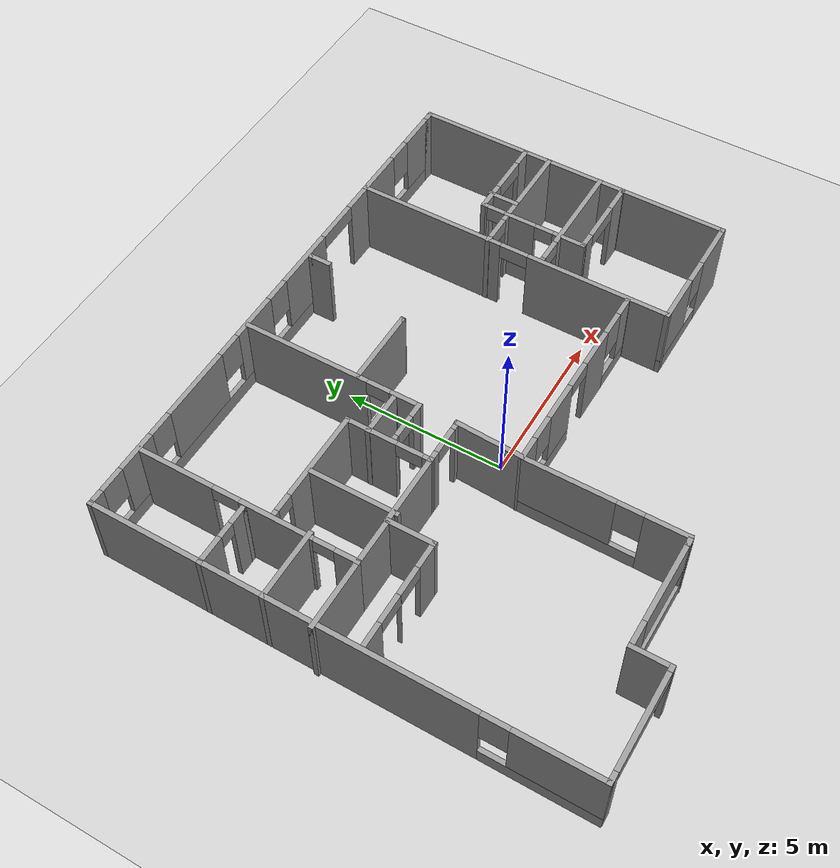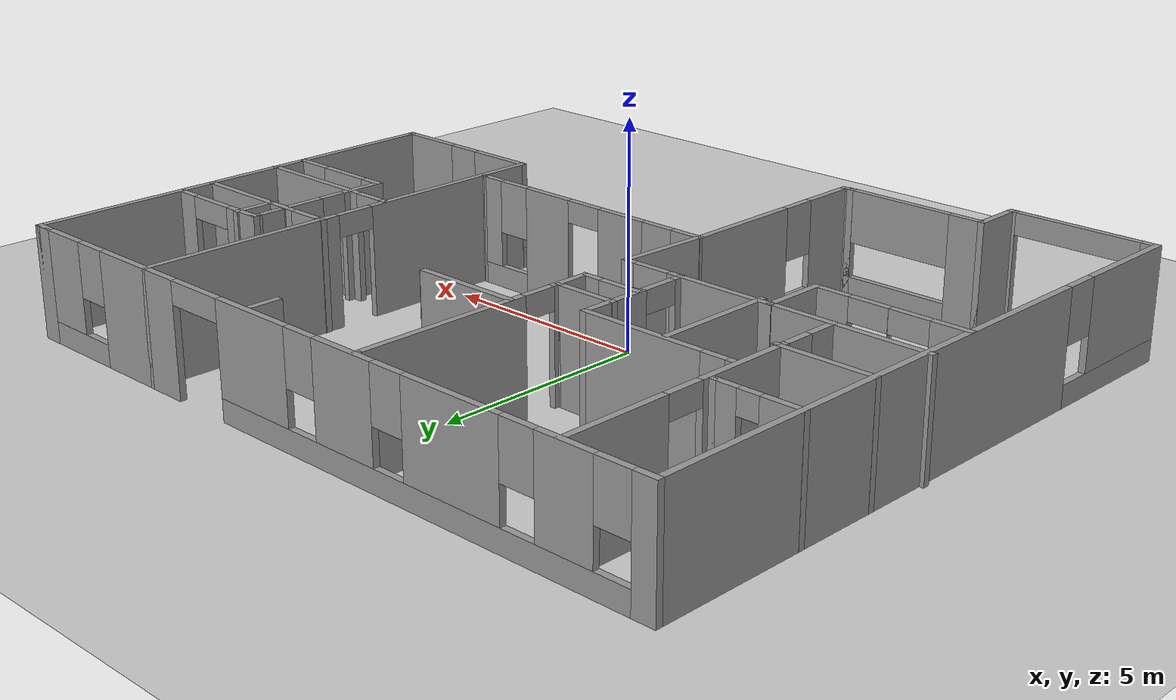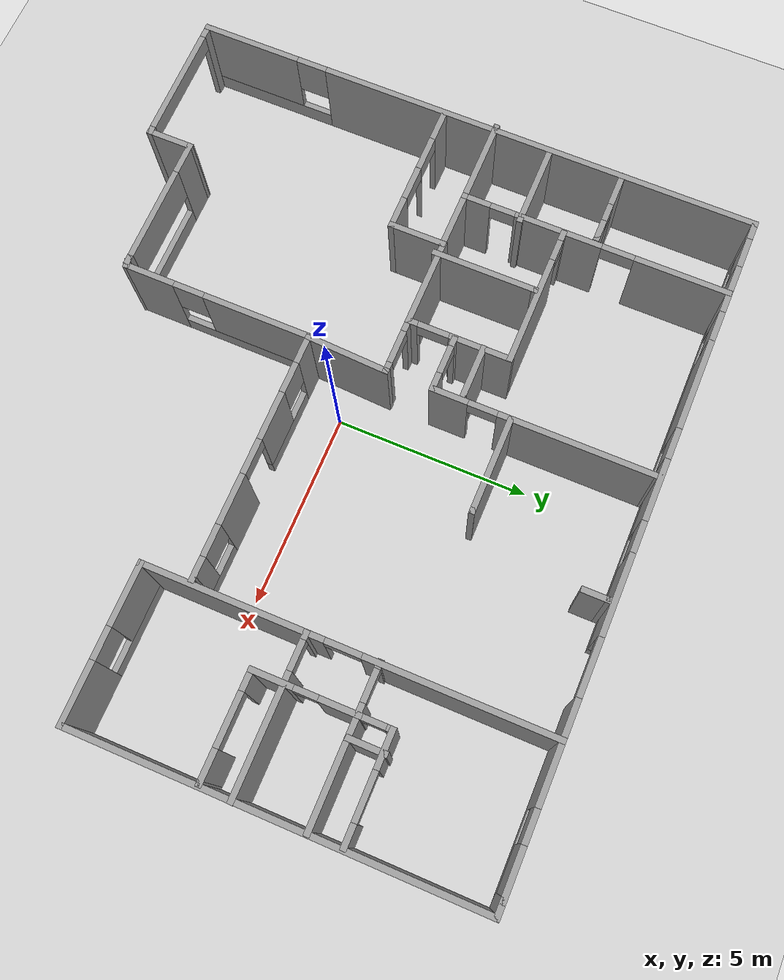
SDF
<sdf version="1.7">
 <world name="default">
  <light name="sun" type="directional">
   <pose>0 0 10 0 -0 0</pose>
   <diffuse>0.8 0.8 0.8 1</diffuse>
   <specular>0.2 0.2 0.2 1</specular>
   <attenuation>
    <range>1000</range>
    <constant>0.9</constant>
    <linear>0.01</linear>
    <quadratic>0.001</quadratic>
   </attenuation>
   <direction>-0.5 0.1 -0.9</direction>
   <spot><inner_angle>0</inner_angle><outer_angle>0</outer_angle><falloff>0</falloff></spot>
  </light>
  <model name="ground_plane">
   <static>1</static>
   <link name="link">
    <collision name="collision">
     <geometry><plane><normal>0 0 1</normal><size>100 100</size></plane></geometry>
     <surface>
      <contact><collide_bitmask>65535</collide_bitmask></contact>
      <friction><ode><mu>100</mu><mu2>50</mu2></ode></friction>
     </surface>
    </collision>
    <visual name="visual">
     <cast_shadows>0</cast_shadows>
     <geometry><plane><normal>0 0 1</normal><size>100 100</size></plane></geometry>
     <material>
      <script><uri>file://media/materials/scripts/gazebo.material</uri><name>Gazebo/Grey</name></script>
     </material>
    </visual>
   </link>
  </model>
  <gravity>0 0 -9.8</gravity>
  <magnetic_field>6e-06 2.3e-05 -4.2e-05</magnetic_field>
  <atmosphere type="adiabatic"/>
  <physics type="ode">
   <max_step_size>0.001</max_step_size>
   <real_time_factor>1</real_time_factor>
   <real_time_update_rate>1000</real_time_update_rate>
  </physics>
  <scene><ambient>0.4 0.4 0.4 1</ambient><background>0.7 0.7 0.7 1</background><shadows>1</shadows></scene>
  <spherical_coordinates>
   <surface_model>EARTH_WGS84</surface_model>
   <latitude_deg>0</latitude_deg>
   <longitude_deg>0</longitude_deg>
   <elevation>0</elevation>
   <heading_deg>0</heading_deg>
  </spherical_coordinates>
  <model name="Floorplan7">
   <pose>0.685617 0.398656 0 0 -0 0</pose>
   <link name="Wall_0">
    <pose>-0.133018 7.425 0 0 -0 0</pose>
    <visual name="Wall_0_Visual_0">
     <pose>-8.24103 0 1.25 0 -0 0</pose>
     <geometry><box><size>0.517936 0.15 2.5</size></box></geometry>
     <material>
      <script><uri>file://media/materials/scripts/gazebo.material</uri><name>Gazebo/Grey</name></script>
      <ambient>1 1 1 1</ambient>
     </material>
     <meta><layer>0</layer></meta>
    </visual>
    <collision name="Wall_0_Collision_0">
     <geometry><box><size>0.517936 0.15 2.5</size></box></geometry>
     <pose>-8.24103 0 1.25 0 -0 0</pose>
    </collision>
    <visual name="Wall_0_Visual_1">
     <pose>5.19319 0 1.25 0 -0 0</pose>
     <geometry><box><size>2.48084 0.15 2.5</size></box></geometry>
     <material>
      <script><uri>file://media/materials/scripts/gazebo.material</uri><name>Gazebo/Grey</name></script>
      <ambient>1 1 1 1</ambient>
     </material>
     <meta><layer>0</layer></meta>
    </visual>
    <collision name="Wall_0_Collision_1">
     <geometry><box><size>2.48084 0.15 2.5</size></box></geometry>
     <pose>5.19319 0 1.25 0 -0 0</pose>
    </collision>
    <visual name="Wall_0_Visual_2">
     <pose>-2.72761 0 0.25 0 -0 0</pose>
     <geometry><box><size>10.5089 0.15 0.5</size></box></geometry>
     <material>
      <script><uri>file://media/materials/scripts/gazebo.material</uri><name>Gazebo/Grey</name></script>
      <ambient>1 1 1 1</ambient>
     </material>
     <meta><layer>0</layer></meta>
    </visual>
    <collision name="Wall_0_Collision_2">
     <geometry><box><size>10.5089 0.15 0.5</size></box></geometry>
     <pose>-2.72761 0 0.25 0 -0 0</pose>
    </collision>
    <visual name="Wall_0_Visual_3">
     <pose>7.4668 0 0.25 0 -0 0</pose>
     <geometry><box><size>2.06639 0.15 0.5</size></box></geometry>
     <material>
      <script><uri>file://media/materials/scripts/gazebo.material</uri><name>Gazebo/Grey</name></script>
      <ambient>1 1 1 1</ambient>
     </material>
     <meta><layer>0</layer></meta>
    </visual>
    <collision name="Wall_0_Collision_3">
     <geometry><box><size>2.06639 0.15 0.5</size></box></geometry>
     <pose>7.4668 0 0.25 0 -0 0</pose>
    </collision>
    <visual name="Wall_0_Visual_4">
     <pose>-6.53696 0 1.5 0 -0 0</pose>
     <geometry><box><size>1.29021 0.15 2</size></box></geometry>
     <material>
      <script><uri>file://media/materials/scripts/gazebo.material</uri><name>Gazebo/Grey</name></script>
      <ambient>1 1 1 1</ambient>
     </material>
     <meta><layer>0</layer></meta>
    </visual>
    <collision name="Wall_0_Collision_4">
     <geometry><box><size>1.29021 0.15 2</size></box></geometry>
     <pose>-6.53696 0 1.5 0 -0 0</pose>
    </collision>
    <visual name="Wall_0_Visual_5">
     <pose>-3.90061 0 1.5 0 -0 0</pose>
     <geometry><box><size>2.38251 0.15 2</size></box></geometry>
     <material>
      <script><uri>file://media/materials/scripts/gazebo.material</uri><name>Gazebo/Grey</name></script>
      <ambient>1 1 1 1</ambient>
     </material>
     <meta><layer>0</layer></meta>
    </visual>
    <collision name="Wall_0_Collision_5">
     <geometry><box><size>2.38251 0.15 2</size></box></geometry>
     <pose>-3.90061 0 1.5 0 -0 0</pose>
    </collision>
    <visual name="Wall_0_Visual_6">
     <pose>-1.11591 0 1.5 0 -0 0</pose>
     <geometry><box><size>1.58688 0.15 2</size></box></geometry>
     <material>
      <script><uri>file://media/materials/scripts/gazebo.material</uri><name>Gazebo/Grey</name></script>
      <ambient>1 1 1 1</ambient>
     </material>
     <meta><layer>0</layer></meta>
    </visual>
    <collision name="Wall_0_Collision_6">
     <geometry><box><size>1.58688 0.15 2</size></box></geometry>
     <pose>-1.11591 0 1.5 0 -0 0</pose>
    </collision>
    <visual name="Wall_0_Visual_7">
     <pose>1.50218 0 1.5 0 -0 0</pose>
     <geometry><box><size>2.04932 0.15 2</size></box></geometry>
     <material>
      <script><uri>file://media/materials/scripts/gazebo.material</uri><name>Gazebo/Grey</name></script>
      <ambient>1 1 1 1</ambient>
     </material>
     <meta><layer>0</layer></meta>
    </visual>
    <collision name="Wall_0_Collision_7">
     <geometry><box><size>2.04932 0.15 2</size></box></geometry>
     <pose>1.50218 0 1.5 0 -0 0</pose>
    </collision>
    <visual name="Wall_0_Visual_8">
     <pose>1.50218 0 1.5 0 -0 0</pose>
     <geometry><box><size>2.04932 0.15 2</size></box></geometry>
     <material>
      <script><uri>file://media/materials/scripts/gazebo.material</uri><name>Gazebo/Grey</name></script>
      <ambient>1 1 1 1</ambient>
     </material>
     <meta><layer>0</layer></meta>
    </visual>
    <collision name="Wall_0_Collision_8">
     <geometry><box><size>2.04932 0.15 2</size></box></geometry>
     <pose>1.50218 0 1.5 0 -0 0</pose>
    </collision>
    <visual name="Wall_0_Visual_9">
     <pose>7.8668 0 1.5 0 -0 0</pose>
     <geometry><box><size>1.26639 0.15 2</size></box></geometry>
     <material>
      <script><uri>file://media/materials/scripts/gazebo.material</uri><name>Gazebo/Grey</name></script>
      <ambient>1 1 1 1</ambient>
     </material>
     <meta><layer>0</layer></meta>
    </visual>
    <collision name="Wall_0_Collision_9">
     <geometry><box><size>1.26639 0.15 2</size></box></geometry>
     <pose>7.8668 0 1.5 0 -0 0</pose>
    </collision>
    <visual name="Wall_0_Visual_10">
     <pose>-7.58206 0 1.9 0 -0 0</pose>
     <geometry><box><size>0.8 0.15 1.2</size></box></geometry>
     <material>
      <script><uri>file://media/materials/scripts/gazebo.material</uri><name>Gazebo/Grey</name></script>
      <ambient>1 1 1 1</ambient>
     </material>
     <meta><layer>0</layer></meta>
    </visual>
    <collision name="Wall_0_Collision_10">
     <geometry><box><size>0.8 0.15 1.2</size></box></geometry>
     <pose>-7.58206 0 1.9 0 -0 0</pose>
    </collision>
    <visual name="Wall_0_Visual_11">
     <pose>6.83361 0 1.9 0 -0 0</pose>
     <geometry><box><size>0.8 0.15 1.2</size></box></geometry>
     <material>
      <script><uri>file://media/materials/scripts/gazebo.material</uri><name>Gazebo/Grey</name></script>
      <ambient>1 1 1 1</ambient>
     </material>
     <meta><layer>0</layer></meta>
    </visual>
    <collision name="Wall_0_Collision_11">
     <geometry><box><size>0.8 0.15 1.2</size></box></geometry>
     <pose>6.83361 0 1.9 0 -0 0</pose>
    </collision>
    <visual name="Wall_0_Visual_12">
     <pose>-5.49186 0 1.9 0 -0 0</pose>
     <geometry><box><size>0.8 0.15 1.2</size></box></geometry>
     <material>
      <script><uri>file://media/materials/scripts/gazebo.material</uri><name>Gazebo/Grey</name></script>
      <ambient>1 1 1 1</ambient>
     </material>
     <meta><layer>0</layer></meta>
    </visual>
    <collision name="Wall_0_Collision_12">
     <geometry><box><size>0.8 0.15 1.2</size></box></geometry>
     <pose>-5.49186 0 1.9 0 -0 0</pose>
    </collision>
    <visual name="Wall_0_Visual_13">
     <pose>-2.30935 0 1.9 0 -0 0</pose>
     <geometry><box><size>0.8 0.15 1.2</size></box></geometry>
     <material>
      <script><uri>file://media/materials/scripts/gazebo.material</uri><name>Gazebo/Grey</name></script>
      <ambient>1 1 1 1</ambient>
     </material>
     <meta><layer>0</layer></meta>
    </visual>
    <collision name="Wall_0_Collision_13">
     <geometry><box><size>0.8 0.15 1.2</size></box></geometry>
     <pose>-2.30935 0 1.9 0 -0 0</pose>
    </collision>
    <visual name="Wall_0_Visual_14">
     <pose>0.077526 0 1.9 0 -0 0</pose>
     <geometry><box><size>0.8 0.15 1.2</size></box></geometry>
     <material>
      <script><uri>file://media/materials/scripts/gazebo.material</uri><name>Gazebo/Grey</name></script>
      <ambient>1 1 1 1</ambient>
     </material>
     <meta><layer>0</layer></meta>
    </visual>
    <collision name="Wall_0_Collision_14">
     <geometry><box><size>0.8 0.15 1.2</size></box></geometry>
     <pose>0.077526 0 1.9 0 -0 0</pose>
    </collision>
    <visual name="Wall_0_Visual_15">
     <pose>3.2398 0 2.25 0 -0 0</pose>
     <geometry><box><size>1.42592 0.15 0.5</size></box></geometry>
     <material>
      <script><uri>file://media/materials/scripts/gazebo.material</uri><name>Gazebo/Grey</name></script>
      <ambient>1 1 1 1</ambient>
     </material>
     <meta><layer>0</layer></meta>
    </visual>
    <collision name="Wall_0_Collision_15">
     <geometry><box><size>1.42592 0.15 0.5</size></box></geometry>
     <pose>3.2398 0 2.25 0 -0 0</pose>
    </collision>
    <visual name="Wall_0_Visual_16">
     <pose>3.2398 0 2.25 0 -0 0</pose>
     <geometry><box><size>1.42592 0.15 0.5</size></box></geometry>
     <material>
      <script><uri>file://media/materials/scripts/gazebo.material</uri><name>Gazebo/Grey</name></script>
      <ambient>1 1 1 1</ambient>
     </material>
     <meta><layer>0</layer></meta>
    </visual>
    <collision name="Wall_0_Collision_16">
     <geometry><box><size>1.42592 0.15 0.5</size></box></geometry>
     <pose>3.2398 0 2.25 0 -0 0</pose>
    </collision>
   </link>
   <link name="Wall_1">
    <collision name="Wall_1_Collision">
     <geometry><box><size>0.5 0.15 2.5</size></box></geometry>
     <pose>0 0 1.25 0 -0 0</pose>
    </collision>
    <visual name="Wall_1_Visual">
     <pose>0 0 1.25 0 -0 0</pose>
     <geometry><box><size>0.5 0.15 2.5</size></box></geometry>
     <material>
      <script><uri>file://media/materials/scripts/gazebo.material</uri><name>Gazebo/Grey</name></script>
      <ambient>1 1 1 1</ambient>
     </material>
     <meta><layer>0</layer></meta>
    </visual>
    <pose>8.46698 7.425 0 0 -0 0</pose>
   </link>
   <link name="Wall_10">
    <collision name="Wall_10_Collision">
     <geometry><box><size>1.25 0.15 2.5</size></box></geometry>
     <pose>0 0 1.25 0 -0 0</pose>
    </collision>
    <visual name="Wall_10_Visual">
     <pose>0 0 1.25 0 -0 0</pose>
     <geometry><box><size>1.25 0.15 2.5</size></box></geometry>
     <material>
      <script><uri>file://media/materials/scripts/gazebo.material</uri><name>Gazebo/Grey</name></script>
      <ambient>1 1 1 1</ambient>
     </material>
     <meta><layer>0</layer></meta>
    </visual>
    <pose>-5.20802 -6.875 0 0 -0 1.5708</pose>
   </link>
   <link name="Wall_11">
    <pose>-3.53302 -6.325 0 0 -0 0</pose>
    <visual name="Wall_11_Visual_0">
     <pose>-1.31856 0 1.25 0 -0 0</pose>
     <geometry><box><size>0.862879 0.15 2.5</size></box></geometry>
     <material>
      <script><uri>file://media/materials/scripts/gazebo.material</uri><name>Gazebo/Grey</name></script>
      <ambient>1 1 1 1</ambient>
     </material>
     <meta><layer>0</layer></meta>
    </visual>
    <collision name="Wall_11_Collision_0">
     <geometry><box><size>0.862879 0.15 2.5</size></box></geometry>
     <pose>-1.31856 0 1.25 0 -0 0</pose>
    </collision>
    <visual name="Wall_11_Visual_1">
     <pose>0.43144 0 0.25 0 -0 0</pose>
     <geometry><box><size>2.63712 0.15 0.5</size></box></geometry>
     <material>
      <script><uri>file://media/materials/scripts/gazebo.material</uri><name>Gazebo/Grey</name></script>
      <ambient>1 1 1 1</ambient>
     </material>
     <meta><layer>0</layer></meta>
    </visual>
    <collision name="Wall_11_Collision_1">
     <geometry><box><size>2.63712 0.15 0.5</size></box></geometry>
     <pose>0.43144 0 0.25 0 -0 0</pose>
    </collision>
    <visual name="Wall_11_Visual_2">
     <pose>1.67426 0 1.5 0 -0 0</pose>
     <geometry><box><size>0.151472 0.15 2</size></box></geometry>
     <material>
      <script><uri>file://media/materials/scripts/gazebo.material</uri><name>Gazebo/Grey</name></script>
      <ambient>1 1 1 1</ambient>
     </material>
     <meta><layer>0</layer></meta>
    </visual>
    <collision name="Wall_11_Collision_2">
     <geometry><box><size>0.151472 0.15 2</size></box></geometry>
     <pose>1.67426 0 1.5 0 -0 0</pose>
    </collision>
    <visual name="Wall_11_Visual_3">
     <pose>0.355704 0 1.9 0 -0 0</pose>
     <geometry><box><size>2.48565 0.15 1.2</size></box></geometry>
     <material>
      <script><uri>file://media/materials/scripts/gazebo.material</uri><name>Gazebo/Grey</name></script>
      <ambient>1 1 1 1</ambient>
     </material>
     <meta><layer>0</layer></meta>
    </visual>
    <collision name="Wall_11_Collision_3">
     <geometry><box><size>2.48565 0.15 1.2</size></box></geometry>
     <pose>0.355704 0 1.9 0 -0 0</pose>
    </collision>
   </link>
   <link name="Wall_12">
    <collision name="Wall_12_Collision">
     <geometry><box><size>0.25 0.15 2.5</size></box></geometry>
     <pose>0 0 1.25 0 -0 0</pose>
    </collision>
    <visual name="Wall_12_Visual">
     <pose>0 0 1.25 0 -0 0</pose>
     <geometry><box><size>0.25 0.15 2.5</size></box></geometry>
     <material>
      <script><uri>file://media/materials/scripts/gazebo.material</uri><name>Gazebo/Grey</name></script>
      <ambient>1 1 1 1</ambient>
     </material>
     <meta><layer>0</layer></meta>
    </visual>
    <pose>-1.80802 -6.325 0 0 -0 0</pose>
   </link>
   <link name="Wall_13">
    <collision name="Wall_13_Collision">
     <geometry><box><size>0.25 0.15 2.5</size></box></geometry>
     <pose>0 0 1.25 0 -0 0</pose>
    </collision>
    <visual name="Wall_13_Visual">
     <pose>0 0 1.25 0 -0 0</pose>
     <geometry><box><size>0.25 0.15 2.5</size></box></geometry>
     <material>
      <script><uri>file://media/materials/scripts/gazebo.material</uri><name>Gazebo/Grey</name></script>
      <ambient>1 1 1 1</ambient>
     </material>
     <meta><layer>0</layer></meta>
    </visual>
    <pose>-1.70972 -6.31206 0 0 -0 0.261799</pose>
   </link>
   <link name="Wall_14">
    <pose>-1.65681 -3.87627 0 0 -0 1.56889</pose>
    <visual name="Wall_14_Visual_0">
     <pose>-1.82183 0 1.25 0 -0 0</pose>
     <geometry><box><size>1.35207 0.15 2.5</size></box></geometry>
     <material>
      <script><uri>file://media/materials/scripts/gazebo.material</uri><name>Gazebo/Grey</name></script>
      <ambient>1 1 1 1</ambient>
     </material>
     <meta><layer>0</layer></meta>
    </visual>
    <collision name="Wall_14_Collision_0">
     <geometry><box><size>1.35207 0.15 2.5</size></box></geometry>
     <pose>-1.82183 0 1.25 0 -0 0</pose>
    </collision>
    <visual name="Wall_14_Visual_1">
     <pose>0.676036 0 0.25 0 -0 0</pose>
     <geometry><box><size>3.64367 0.15 0.5</size></box></geometry>
     <material>
      <script><uri>file://media/materials/scripts/gazebo.material</uri><name>Gazebo/Grey</name></script>
      <ambient>1 1 1 1</ambient>
     </material>
     <meta><layer>0</layer></meta>
    </visual>
    <collision name="Wall_14_Collision_1">
     <geometry><box><size>3.64367 0.15 0.5</size></box></geometry>
     <pose>0.676036 0 0.25 0 -0 0</pose>
    </collision>
    <visual name="Wall_14_Visual_2">
     <pose>1.07604 0 1.5 0 -0 0</pose>
     <geometry><box><size>2.84367 0.15 2</size></box></geometry>
     <material>
      <script><uri>file://media/materials/scripts/gazebo.material</uri><name>Gazebo/Grey</name></script>
      <ambient>1 1 1 1</ambient>
     </material>
     <meta><layer>0</layer></meta>
    </visual>
    <collision name="Wall_14_Collision_2">
     <geometry><box><size>2.84367 0.15 2</size></box></geometry>
     <pose>1.07604 0 1.5 0 -0 0</pose>
    </collision>
    <visual name="Wall_14_Visual_3">
     <pose>-0.745799 0 1.9 0 -0 0</pose>
     <geometry><box><size>0.8 0.15 1.2</size></box></geometry>
     <material>
      <script><uri>file://media/materials/scripts/gazebo.material</uri><name>Gazebo/Grey</name></script>
      <ambient>1 1 1 1</ambient>
     </material>
     <meta><layer>0</layer></meta>
    </visual>
    <collision name="Wall_14_Collision_3">
     <geometry><box><size>0.8 0.15 1.2</size></box></geometry>
     <pose>-0.745799 0 1.9 0 -0 0</pose>
    </collision>
   </link>
   <link name="Wall_15">
    <pose>1.51819 -1.45127 0 0 -0 0.00068</pose>
    <visual name="Wall_15_Visual_0">
     <pose>-2.84549 0 1.25 0 -0 0</pose>
     <geometry><box><size>0.799793 0.15 2.5</size></box></geometry>
     <material>
      <script><uri>file://media/materials/scripts/gazebo.material</uri><name>Gazebo/Grey</name></script>
      <ambient>1 1 1 1</ambient>
     </material>
     <meta><layer>0</layer></meta>
    </visual>
    <collision name="Wall_15_Collision_0">
     <geometry><box><size>0.799793 0.15 2.5</size></box></geometry>
     <pose>-2.84549 0 1.25 0 -0 0</pose>
    </collision>
    <visual name="Wall_15_Visual_1">
     <pose>1.15507 0 1.25 0 -0 0</pose>
     <geometry><box><size>1.29419 0.15 2.5</size></box></geometry>
     <material>
      <script><uri>file://media/materials/scripts/gazebo.material</uri><name>Gazebo/Grey</name></script>
      <ambient>1 1 1 1</ambient>
     </material>
     <meta><layer>0</layer></meta>
    </visual>
    <collision name="Wall_15_Collision_1">
     <geometry><box><size>1.29419 0.15 2.5</size></box></geometry>
     <pose>1.15507 0 1.25 0 -0 0</pose>
    </collision>
    <visual name="Wall_15_Visual_2">
     <pose>-1.41881 0 0.25 0 -0 0</pose>
     <geometry><box><size>2.05357 0.15 0.5</size></box></geometry>
     <material>
      <script><uri>file://media/materials/scripts/gazebo.material</uri><name>Gazebo/Grey</name></script>
      <ambient>1 1 1 1</ambient>
     </material>
     <meta><layer>0</layer></meta>
    </visual>
    <collision name="Wall_15_Collision_2">
     <geometry><box><size>2.05357 0.15 0.5</size></box></geometry>
     <pose>-1.41881 0 0.25 0 -0 0</pose>
    </collision>
    <visual name="Wall_15_Visual_3">
     <pose>2.52378 0 0.25 0 -0 0</pose>
     <geometry><box><size>1.44322 0.15 0.5</size></box></geometry>
     <material>
      <script><uri>file://media/materials/scripts/gazebo.material</uri><name>Gazebo/Grey</name></script>
      <ambient>1 1 1 1</ambient>
     </material>
     <meta><layer>0</layer></meta>
    </visual>
    <collision name="Wall_15_Collision_3">
     <geometry><box><size>1.44322 0.15 0.5</size></box></geometry>
     <pose>2.52378 0 0.25 0 -0 0</pose>
    </collision>
    <visual name="Wall_15_Visual_4">
     <pose>-1.01881 0 1.5 0 -0 0</pose>
     <geometry><box><size>1.25357 0.15 2</size></box></geometry>
     <material>
      <script><uri>file://media/materials/scripts/gazebo.material</uri><name>Gazebo/Grey</name></script>
      <ambient>1 1 1 1</ambient>
     </material>
     <meta><layer>0</layer></meta>
    </visual>
    <collision name="Wall_15_Collision_4">
     <geometry><box><size>1.25357 0.15 2</size></box></geometry>
     <pose>-1.01881 0 1.5 0 -0 0</pose>
    </collision>
    <visual name="Wall_15_Visual_5">
     <pose>-1.01881 0 1.5 0 -0 0</pose>
     <geometry><box><size>1.25357 0.15 2</size></box></geometry>
     <material>
      <script><uri>file://media/materials/scripts/gazebo.material</uri><name>Gazebo/Grey</name></script>
      <ambient>1 1 1 1</ambient>
     </material>
     <meta><layer>0</layer></meta>
    </visual>
    <collision name="Wall_15_Collision_5">
     <geometry><box><size>1.25357 0.15 2</size></box></geometry>
     <pose>-1.01881 0 1.5 0 -0 0</pose>
    </collision>
    <visual name="Wall_15_Visual_6">
     <pose>2.92378 0 1.5 0 -0 0</pose>
     <geometry><box><size>0.643216 0.15 2</size></box></geometry>
     <material>
      <script><uri>file://media/materials/scripts/gazebo.material</uri><name>Gazebo/Grey</name></script>
      <ambient>1 1 1 1</ambient>
     </material>
     <meta><layer>0</layer></meta>
    </visual>
    <collision name="Wall_15_Collision_6">
     <geometry><box><size>0.643216 0.15 2</size></box></geometry>
     <pose>2.92378 0 1.5 0 -0 0</pose>
    </collision>
    <visual name="Wall_15_Visual_7">
     <pose>-2.04559 0 1.9 0 -0 0</pose>
     <geometry><box><size>0.8 0.15 1.2</size></box></geometry>
     <material>
      <script><uri>file://media/materials/scripts/gazebo.material</uri><name>Gazebo/Grey</name></script>
      <ambient>1 1 1 1</ambient>
     </material>
     <meta><layer>0</layer></meta>
    </visual>
    <collision name="Wall_15_Collision_7">
     <geometry><box><size>0.8 0.15 1.2</size></box></geometry>
     <pose>-2.04559 0 1.9 0 -0 0</pose>
    </collision>
    <visual name="Wall_15_Visual_8">
     <pose>2.20217 0 1.9 0 -0 0</pose>
     <geometry><box><size>0.8 0.15 1.2</size></box></geometry>
     <material>
      <script><uri>file://media/materials/scripts/gazebo.material</uri><name>Gazebo/Grey</name></script>
      <ambient>1 1 1 1</ambient>
     </material>
     <meta><layer>0</layer></meta>
    </visual>
    <collision name="Wall_15_Collision_8">
     <geometry><box><size>0.8 0.15 1.2</size></box></geometry>
     <pose>2.20217 0 1.9 0 -0 0</pose>
    </collision>
    <visual name="Wall_15_Visual_9">
     <pose>0.057978 0 2.25 0 -0 0</pose>
     <geometry><box><size>0.9 0.15 0.5</size></box></geometry>
     <material>
      <script><uri>file://media/materials/scripts/gazebo.material</uri><name>Gazebo/Grey</name></script>
      <ambient>1 1 1 1</ambient>
     </material>
     <meta><layer>0</layer></meta>
    </visual>
    <collision name="Wall_15_Collision_9">
     <geometry><box><size>0.9 0.15 0.5</size></box></geometry>
     <pose>0.057978 0 2.25 0 -0 0</pose>
    </collision>
    <visual name="Wall_15_Visual_10">
     <pose>0.057978 0 2.25 0 -0 0</pose>
     <geometry><box><size>0.9 0.15 0.5</size></box></geometry>
     <material>
      <script><uri>file://media/materials/scripts/gazebo.material</uri><name>Gazebo/Grey</name></script>
      <ambient>1 1 1 1</ambient>
     </material>
     <meta><layer>0</layer></meta>
    </visual>
    <collision name="Wall_15_Collision_10">
     <geometry><box><size>0.9 0.15 0.5</size></box></geometry>
     <pose>0.057978 0 2.25 0 -0 0</pose>
    </collision>
   </link>
   <link name="Wall_16">
    <collision name="Wall_16_Collision">
     <geometry><box><size>0.15 0.15 2.5</size></box></geometry>
     <pose>0 0 1.25 0 -0 0</pose>
    </collision>
    <visual name="Wall_16_Visual">
     <pose>0 0 1.25 0 -0 0</pose>
     <geometry><box><size>0.15 0.15 2.5</size></box></geometry>
     <material>
      <script><uri>file://media/materials/scripts/gazebo.material</uri><name>Gazebo/Grey</name></script>
      <ambient>1 1 1 1</ambient>
     </material>
     <meta><layer>0</layer></meta>
    </visual>
    <pose>4.68858 -1.44912 0 0 -0 0</pose>
   </link>
   <link name="Wall_18">
    <pose>-6.54918 3.98735 0 0 -0 -1.5708</pose>
    <visual name="Wall_18_Visual_0">
     <pose>-2.2619 0 1.25 0 -0 0</pose>
     <geometry><box><size>2.47621 0.15 2.5</size></box></geometry>
     <material>
      <script><uri>file://media/materials/scripts/gazebo.material</uri><name>Gazebo/Grey</name></script>
      <ambient>1 1 1 1</ambient>
     </material>
     <meta><layer>0</layer></meta>
    </visual>
    <collision name="Wall_18_Collision_0">
     <geometry><box><size>2.47621 0.15 2.5</size></box></geometry>
     <pose>-2.2619 0 1.25 0 -0 0</pose>
    </collision>
    <visual name="Wall_18_Visual_1">
     <pose>0.956775 0 1.25 0 -0 0</pose>
     <geometry><box><size>2.26902 0.15 2.5</size></box></geometry>
     <material>
      <script><uri>file://media/materials/scripts/gazebo.material</uri><name>Gazebo/Grey</name></script>
      <ambient>1 1 1 1</ambient>
     </material>
     <meta><layer>0</layer></meta>
    </visual>
    <collision name="Wall_18_Collision_1">
     <geometry><box><size>2.26902 0.15 2.5</size></box></geometry>
     <pose>0.956775 0 1.25 0 -0 0</pose>
    </collision>
    <visual name="Wall_18_Visual_2">
     <pose>3.11753 0 1.25 0 -0 0</pose>
     <geometry><box><size>0.764934 0.15 2.5</size></box></geometry>
     <material>
      <script><uri>file://media/materials/scripts/gazebo.material</uri><name>Gazebo/Grey</name></script>
      <ambient>1 1 1 1</ambient>
     </material>
     <meta><layer>0</layer></meta>
    </visual>
    <collision name="Wall_18_Collision_2">
     <geometry><box><size>0.764934 0.15 2.5</size></box></geometry>
     <pose>3.11753 0 1.25 0 -0 0</pose>
    </collision>
    <visual name="Wall_18_Visual_3">
     <pose>-0.600765 0 2.25 0 -0 0</pose>
     <geometry><box><size>0.846059 0.15 0.5</size></box></geometry>
     <material>
      <script><uri>file://media/materials/scripts/gazebo.material</uri><name>Gazebo/Grey</name></script>
      <ambient>1 1 1 1</ambient>
     </material>
     <meta><layer>0</layer></meta>
    </visual>
    <collision name="Wall_18_Collision_3">
     <geometry><box><size>0.846059 0.15 0.5</size></box></geometry>
     <pose>-0.600765 0 2.25 0 -0 0</pose>
    </collision>
    <visual name="Wall_18_Visual_4">
     <pose>2.41317 0 2.25 0 -0 0</pose>
     <geometry><box><size>0.643781 0.15 0.5</size></box></geometry>
     <material>
      <script><uri>file://media/materials/scripts/gazebo.material</uri><name>Gazebo/Grey</name></script>
      <ambient>1 1 1 1</ambient>
     </material>
     <meta><layer>0</layer></meta>
    </visual>
    <collision name="Wall_18_Collision_4">
     <geometry><box><size>0.643781 0.15 0.5</size></box></geometry>
     <pose>2.41317 0 2.25 0 -0 0</pose>
    </collision>
   </link>
   <link name="Wall_19">
    <collision name="Wall_19_Collision">
     <geometry><box><size>2.25 0.15 2.5</size></box></geometry>
     <pose>0 0 1.25 0 -0 0</pose>
    </collision>
    <visual name="Wall_19_Visual">
     <pose>0 0 1.25 0 -0 0</pose>
     <geometry><box><size>2.25 0.15 2.5</size></box></geometry>
     <material>
      <script><uri>file://media/materials/scripts/gazebo.material</uri><name>Gazebo/Grey</name></script>
      <ambient>1 1 1 1</ambient>
     </material>
     <meta><layer>0</layer></meta>
    </visual>
    <pose>-7.59918 0.562349 0 0 -0 3.14159</pose>
   </link>
   <link name="Wall_2">
    <collision name="Wall_2_Collision">
     <geometry><box><size>10.25 0.15 2.5</size></box></geometry>
     <pose>0 0 1.25 0 -0 0</pose>
    </collision>
    <visual name="Wall_2_Visual">
     <pose>0 0 1.25 0 -0 0</pose>
     <geometry><box><size>10.25 0.15 2.5</size></box></geometry>
     <material>
      <script><uri>file://media/materials/scripts/gazebo.material</uri><name>Gazebo/Grey</name></script>
      <ambient>1 1 1 1</ambient>
     </material>
     <meta><layer>0</layer></meta>
    </visual>
    <pose>8.64198 2.375 0 0 -0 -1.5708</pose>
   </link>
   <link name="Wall_20">
    <collision name="Wall_20_Collision">
     <geometry><box><size>0.15 0.15 2.5</size></box></geometry>
     <pose>0 0 1.25 0 -0 0</pose>
    </collision>
    <visual name="Wall_20_Visual">
     <pose>0 0 1.25 0 -0 0</pose>
     <geometry><box><size>0.15 0.15 2.5</size></box></geometry>
     <material>
      <script><uri>file://media/materials/scripts/gazebo.material</uri><name>Gazebo/Grey</name></script>
      <ambient>1 1 1 1</ambient>
     </material>
     <meta><layer>0</layer></meta>
    </visual>
    <pose>-8.64918 0.562349 0 0 -0 0</pose>
   </link>
   <link name="Wall_22">
    <pose>-6.83525 -0.793988 0 0 -0 0</pose>
    <visual name="Wall_22_Visual_0">
     <pose>-1.33924 0 1.25 0 -0 0</pose>
     <geometry><box><size>0.881865 0.15 2.5</size></box></geometry>
     <material>
      <script><uri>file://media/materials/scripts/gazebo.material</uri><name>Gazebo/Grey</name></script>
      <ambient>1 1 1 1</ambient>
     </material>
     <meta><layer>0</layer></meta>
    </visual>
    <collision name="Wall_22_Collision_0">
     <geometry><box><size>0.881865 0.15 2.5</size></box></geometry>
     <pose>-1.33924 0 1.25 0 -0 0</pose>
    </collision>
    <visual name="Wall_22_Visual_1">
     <pose>0.003448 0 1.25 0 -0 0</pose>
     <geometry><box><size>0.003508 0.15 2.5</size></box></geometry>
     <material>
      <script><uri>file://media/materials/scripts/gazebo.material</uri><name>Gazebo/Grey</name></script>
      <ambient>1 1 1 1</ambient>
     </material>
     <meta><layer>0</layer></meta>
    </visual>
    <collision name="Wall_22_Collision_1">
     <geometry><box><size>0.003508 0.15 2.5</size></box></geometry>
     <pose>0.003448 0 1.25 0 -0 0</pose>
    </collision>
    <visual name="Wall_22_Visual_2">
     <pose>1.34269 0 1.25 0 -0 0</pose>
     <geometry><box><size>0.874968 0.15 2.5</size></box></geometry>
     <material>
      <script><uri>file://media/materials/scripts/gazebo.material</uri><name>Gazebo/Grey</name></script>
      <ambient>1 1 1 1</ambient>
     </material>
     <meta><layer>0</layer></meta>
    </visual>
    <collision name="Wall_22_Collision_2">
     <geometry><box><size>0.874968 0.15 2.5</size></box></geometry>
     <pose>1.34269 0 1.25 0 -0 0</pose>
    </collision>
    <visual name="Wall_22_Visual_3">
     <pose>-0.448306 0 2.25 0 -0 0</pose>
     <geometry><box><size>0.9 0.15 0.5</size></box></geometry>
     <material>
      <script><uri>file://media/materials/scripts/gazebo.material</uri><name>Gazebo/Grey</name></script>
      <ambient>1 1 1 1</ambient>
     </material>
     <meta><layer>0</layer></meta>
    </visual>
    <collision name="Wall_22_Collision_3">
     <geometry><box><size>0.9 0.15 0.5</size></box></geometry>
     <pose>-0.448306 0 2.25 0 -0 0</pose>
    </collision>
    <visual name="Wall_22_Visual_4">
     <pose>0.455202 0 2.25 0 -0 0</pose>
     <geometry><box><size>0.9 0.15 0.5</size></box></geometry>
     <material>
      <script><uri>file://media/materials/scripts/gazebo.material</uri><name>Gazebo/Grey</name></script>
      <ambient>1 1 1 1</ambient>
     </material>
     <meta><layer>0</layer></meta>
    </visual>
    <collision name="Wall_22_Collision_4">
     <geometry><box><size>0.9 0.15 0.5</size></box></geometry>
     <pose>0.455202 0 2.25 0 -0 0</pose>
    </collision>
   </link>
   <link name="Wall_23">
    <collision name="Wall_23_Collision">
     <geometry><box><size>1.5 0.15 2.5</size></box></geometry>
     <pose>0 0 1.25 0 -0 0</pose>
    </collision>
    <visual name="Wall_23_Visual">
     <pose>0 0 1.25 0 -0 0</pose>
     <geometry><box><size>1.5 0.15 2.5</size></box></geometry>
     <material>
      <script><uri>file://media/materials/scripts/gazebo.material</uri><name>Gazebo/Grey</name></script>
      <ambient>1 1 1 1</ambient>
     </material>
     <meta><layer>0</layer></meta>
    </visual>
    <pose>-5.13008 -0.118989 0 0 -0 1.5708</pose>
   </link>
   <link name="Wall_24">
    <collision name="Wall_24_Collision">
     <geometry><box><size>1.56911 0.15 2.5</size></box></geometry>
     <pose>0 0 1.25 0 -0 0</pose>
    </collision>
    <visual name="Wall_24_Visual">
     <pose>0 0 1.25 0 -0 0</pose>
     <geometry><box><size>1.56911 0.15 2.5</size></box></geometry>
     <material>
      <script><uri>file://media/materials/scripts/gazebo.material</uri><name>Gazebo/Grey</name></script>
      <ambient>1 1 1 1</ambient>
     </material>
     <meta><layer>0</layer></meta>
    </visual>
    <pose>-5.83963 0.55918 0 0 -0 3.13713</pose>
   </link>
   <link name="Wall_25">
    <collision name="Wall_25_Collision">
     <geometry><box><size>0.15 0.15 2.5</size></box></geometry>
     <pose>0 0 1.25 0 -0 0</pose>
    </collision>
    <visual name="Wall_25_Visual">
     <pose>0 0 1.25 0 -0 0</pose>
     <geometry><box><size>0.15 0.15 2.5</size></box></geometry>
     <material>
      <script><uri>file://media/materials/scripts/gazebo.material</uri><name>Gazebo/Grey</name></script>
      <ambient>1 1 1 1</ambient>
     </material>
     <meta><layer>0</layer></meta>
    </visual>
    <pose>-6.54918 0.562349 0 0 -0 0</pose>
   </link>
   <link name="Wall_27">
    <collision name="Wall_27_Collision">
     <geometry><box><size>2.25 0.15 2.5</size></box></geometry>
     <pose>0 0 1.25 0 -0 0</pose>
    </collision>
    <visual name="Wall_27_Visual">
     <pose>0 0 1.25 0 -0 0</pose>
     <geometry><box><size>2.25 0.15 2.5</size></box></geometry>
     <material>
      <script><uri>file://media/materials/scripts/gazebo.material</uri><name>Gazebo/Grey</name></script>
      <ambient>1 1 1 1</ambient>
     </material>
     <meta><layer>0</layer></meta>
    </visual>
    <pose>-7.51053 2.06214 0 0 -0 0</pose>
   </link>
   <link name="Wall_28">
    <collision name="Wall_28_Collision">
     <geometry><box><size>0.15 0.15 2.5</size></box></geometry>
     <pose>0 0 1.25 0 -0 0</pose>
    </collision>
    <visual name="Wall_28_Visual">
     <pose>0 0 1.25 0 -0 0</pose>
     <geometry><box><size>0.15 0.15 2.5</size></box></geometry>
     <material>
      <script><uri>file://media/materials/scripts/gazebo.material</uri><name>Gazebo/Grey</name></script>
      <ambient>1 1 1 1</ambient>
     </material>
     <meta><layer>0</layer></meta>
    </visual>
    <pose>-6.46053 2.06214 0 0 -0 0</pose>
   </link>
   <link name="Wall_3">
    <collision name="Wall_3_Collision">
     <geometry><box><size>0.15 0.15 2.5</size></box></geometry>
     <pose>0 0 1.25 0 -0 0</pose>
    </collision>
    <visual name="Wall_3_Visual">
     <pose>0 0 1.25 0 -0 0</pose>
     <geometry><box><size>0.15 0.15 2.5</size></box></geometry>
     <material>
      <script><uri>file://media/materials/scripts/gazebo.material</uri><name>Gazebo/Grey</name></script>
      <ambient>1 1 1 1</ambient>
     </material>
     <meta><layer>0</layer></meta>
    </visual>
    <pose>8.64198 -2.675 0 0 -0 0</pose>
   </link>
   <link name="Wall_30">
    <pose>-7.63553 3.97293 0 0 -0 0</pose>
    <visual name="Wall_30_Visual_0">
     <pose>-0.538897 0 1.25 0 -0 0</pose>
     <geometry><box><size>0.922206 0.15 2.5</size></box></geometry>
     <material>
      <script><uri>file://media/materials/scripts/gazebo.material</uri><name>Gazebo/Grey</name></script>
      <ambient>1 1 1 1</ambient>
     </material>
     <meta><layer>0</layer></meta>
    </visual>
    <collision name="Wall_30_Collision_0">
     <geometry><box><size>0.922206 0.15 2.5</size></box></geometry>
     <pose>-0.538897 0 1.25 0 -0 0</pose>
    </collision>
    <visual name="Wall_30_Visual_1">
     <pose>0.702083 0 1.25 0 -0 0</pose>
     <geometry><box><size>0.595835 0.15 2.5</size></box></geometry>
     <material>
      <script><uri>file://media/materials/scripts/gazebo.material</uri><name>Gazebo/Grey</name></script>
      <ambient>1 1 1 1</ambient>
     </material>
     <meta><layer>0</layer></meta>
    </visual>
    <collision name="Wall_30_Collision_1">
     <geometry><box><size>0.595835 0.15 2.5</size></box></geometry>
     <pose>0.702083 0 1.25 0 -0 0</pose>
    </collision>
    <visual name="Wall_30_Visual_2">
     <pose>0.163186 0 2.25 0 -0 0</pose>
     <geometry><box><size>0.481959 0.15 0.5</size></box></geometry>
     <material>
      <script><uri>file://media/materials/scripts/gazebo.material</uri><name>Gazebo/Grey</name></script>
      <ambient>1 1 1 1</ambient>
     </material>
     <meta><layer>0</layer></meta>
    </visual>
    <collision name="Wall_30_Collision_2">
     <geometry><box><size>0.481959 0.15 0.5</size></box></geometry>
     <pose>0.163186 0 2.25 0 -0 0</pose>
    </collision>
   </link>
   <link name="Wall_31">
    <collision name="Wall_31_Collision">
     <geometry><box><size>0.15 0.15 2.5</size></box></geometry>
     <pose>0 0 1.25 0 -0 0</pose>
    </collision>
    <visual name="Wall_31_Visual">
     <pose>0 0 1.25 0 -0 0</pose>
     <geometry><box><size>0.15 0.15 2.5</size></box></geometry>
     <material>
      <script><uri>file://media/materials/scripts/gazebo.material</uri><name>Gazebo/Grey</name></script>
      <ambient>1 1 1 1</ambient>
     </material>
     <meta><layer>0</layer></meta>
    </visual>
    <pose>-6.71053 3.97293 0 0 -0 0</pose>
   </link>
   <link name="Wall_33">
    <pose>-4.7387 3.17612 0 0 -0 0</pose>
    <visual name="Wall_33_Visual_0">
     <pose>-1.71604 0 1.25 0 -0 0</pose>
     <geometry><box><size>0.287751 0.15 2.5</size></box></geometry>
     <material>
      <script><uri>file://media/materials/scripts/gazebo.material</uri><name>Gazebo/Grey</name></script>
      <ambient>1 1 1 1</ambient>
     </material>
     <meta><layer>0</layer></meta>
    </visual>
    <collision name="Wall_33_Collision_0">
     <geometry><box><size>0.287751 0.15 2.5</size></box></geometry>
     <pose>-1.71604 0 1.25 0 -0 0</pose>
    </collision>
    <visual name="Wall_33_Visual_1">
     <pose>0.42531 0 1.25 0 -0 0</pose>
     <geometry><box><size>2.86921 0.15 2.5</size></box></geometry>
     <material>
      <script><uri>file://media/materials/scripts/gazebo.material</uri><name>Gazebo/Grey</name></script>
      <ambient>1 1 1 1</ambient>
     </material>
     <meta><layer>0</layer></meta>
    </visual>
    <collision name="Wall_33_Collision_1">
     <geometry><box><size>2.86921 0.15 2.5</size></box></geometry>
     <pose>0.42531 0 1.25 0 -0 0</pose>
    </collision>
    <visual name="Wall_33_Visual_2">
     <pose>-1.29073 0 2.25 0 -0 0</pose>
     <geometry><box><size>0.56287 0.15 0.5</size></box></geometry>
     <material>
      <script><uri>file://media/materials/scripts/gazebo.material</uri><name>Gazebo/Grey</name></script>
      <ambient>1 1 1 1</ambient>
     </material>
     <meta><layer>0</layer></meta>
    </visual>
    <collision name="Wall_33_Collision_2">
     <geometry><box><size>0.56287 0.15 0.5</size></box></geometry>
     <pose>-1.29073 0 2.25 0 -0 0</pose>
    </collision>
   </link>
   <link name="Wall_34">
    <pose>-2.94373 1.87613 0 0 -0 -1.5708</pose>
    <visual name="Wall_34_Visual_0">
     <pose>-0.559246 0 1.25 0 -0 0</pose>
     <geometry><box><size>1.63151 0.15 2.5</size></box></geometry>
     <material>
      <script><uri>file://media/materials/scripts/gazebo.material</uri><name>Gazebo/Grey</name></script>
      <ambient>1 1 1 1</ambient>
     </material>
     <meta><layer>0</layer></meta>
    </visual>
    <collision name="Wall_34_Collision_0">
     <geometry><box><size>1.63151 0.15 2.5</size></box></geometry>
     <pose>-0.559246 0 1.25 0 -0 0</pose>
    </collision>
    <visual name="Wall_34_Visual_1">
     <pose>1.21856 0 1.25 0 -0 0</pose>
     <geometry><box><size>0.312889 0.15 2.5</size></box></geometry>
     <material>
      <script><uri>file://media/materials/scripts/gazebo.material</uri><name>Gazebo/Grey</name></script>
      <ambient>1 1 1 1</ambient>
     </material>
     <meta><layer>0</layer></meta>
    </visual>
    <collision name="Wall_34_Collision_1">
     <geometry><box><size>0.312889 0.15 2.5</size></box></geometry>
     <pose>1.21856 0 1.25 0 -0 0</pose>
    </collision>
    <visual name="Wall_34_Visual_2">
     <pose>0.659309 0 2.25 0 -0 0</pose>
     <geometry><box><size>0.805604 0.15 0.5</size></box></geometry>
     <material>
      <script><uri>file://media/materials/scripts/gazebo.material</uri><name>Gazebo/Grey</name></script>
      <ambient>1 1 1 1</ambient>
     </material>
     <meta><layer>0</layer></meta>
    </visual>
    <collision name="Wall_34_Collision_2">
     <geometry><box><size>0.805604 0.15 0.5</size></box></geometry>
     <pose>0.659309 0 2.25 0 -0 0</pose>
    </collision>
   </link>
   <link name="Wall_35">
    <collision name="Wall_35_Collision">
     <geometry><box><size>2.33635 0.15 2.5</size></box></geometry>
     <pose>0 0 1.25 0 -0 0</pose>
    </collision>
    <visual name="Wall_35_Visual">
     <pose>0 0 1.25 0 -0 0</pose>
     <geometry><box><size>2.33635 0.15 2.5</size></box></geometry>
     <material>
      <script><uri>file://media/materials/scripts/gazebo.material</uri><name>Gazebo/Grey</name></script>
      <ambient>1 1 1 1</ambient>
     </material>
     <meta><layer>0</layer></meta>
    </visual>
    <pose>-4.03691 0.576125 0 0 -0 3.14159</pose>
   </link>
   <link name="Wall_36">
    <collision name="Wall_36_Collision">
     <geometry><box><size>0.15 0.15 2.5</size></box></geometry>
     <pose>0 0 1.25 0 -0 0</pose>
    </collision>
    <visual name="Wall_36_Visual">
     <pose>0 0 1.25 0 -0 0</pose>
     <geometry><box><size>0.15 0.15 2.5</size></box></geometry>
     <material>
      <script><uri>file://media/materials/scripts/gazebo.material</uri><name>Gazebo/Grey</name></script>
      <ambient>1 1 1 1</ambient>
     </material>
     <meta><layer>0</layer></meta>
    </visual>
    <pose>-5.13008 0.556011 0 0 -0 0</pose>
   </link>
   <link name="Wall_38">
    <collision name="Wall_38_Collision">
     <geometry><box><size>2.75 0.15 2.5</size></box></geometry>
     <pose>0 0 1.25 0 -0 0</pose>
    </collision>
    <visual name="Wall_38_Visual">
     <pose>0 0 1.25 0 -0 0</pose>
     <geometry><box><size>2.75 0.15 2.5</size></box></geometry>
     <material>
      <script><uri>file://media/materials/scripts/gazebo.material</uri><name>Gazebo/Grey</name></script>
      <ambient>1 1 1 1</ambient>
     </material>
     <meta><layer>0</layer></meta>
    </visual>
    <pose>-4.83903 1.77689 0 0 -0 1.5708</pose>
   </link>
   <link name="Wall_39">
    <collision name="Wall_39_Collision">
     <geometry><box><size>0.15 0.15 2.5</size></box></geometry>
     <pose>0 0 1.25 0 -0 0</pose>
    </collision>
    <visual name="Wall_39_Visual">
     <pose>0 0 1.25 0 -0 0</pose>
     <geometry><box><size>0.15 0.15 2.5</size></box></geometry>
     <material>
      <script><uri>file://media/materials/scripts/gazebo.material</uri><name>Gazebo/Grey</name></script>
      <ambient>1 1 1 1</ambient>
     </material>
     <meta><layer>0</layer></meta>
    </visual>
    <pose>-4.83903 3.07689 0 0 -0 0</pose>
   </link>
   <link name="Wall_4">
    <pose>6.71698 -2.675 0 0 -0 3.14159</pose>
    <visual name="Wall_4_Visual_0">
     <pose>-1.20529 0 1.25 0 -0 0</pose>
     <geometry><box><size>1.58942 0.15 2.5</size></box></geometry>
     <material>
      <script><uri>file://media/materials/scripts/gazebo.material</uri><name>Gazebo/Grey</name></script>
      <ambient>1 1 1 1</ambient>
     </material>
     <meta><layer>0</layer></meta>
    </visual>
    <collision name="Wall_4_Collision_0">
     <geometry><box><size>1.58942 0.15 2.5</size></box></geometry>
     <pose>-1.20529 0 1.25 0 -0 0</pose>
    </collision>
    <visual name="Wall_4_Visual_1">
     <pose>0.794711 0 0.25 0 -0 0</pose>
     <geometry><box><size>2.41058 0.15 0.5</size></box></geometry>
     <material>
      <script><uri>file://media/materials/scripts/gazebo.material</uri><name>Gazebo/Grey</name></script>
      <ambient>1 1 1 1</ambient>
     </material>
     <meta><layer>0</layer></meta>
    </visual>
    <collision name="Wall_4_Collision_1">
     <geometry><box><size>2.41058 0.15 0.5</size></box></geometry>
     <pose>0.794711 0 0.25 0 -0 0</pose>
    </collision>
    <visual name="Wall_4_Visual_2">
     <pose>1.19471 0 1.5 0 -0 0</pose>
     <geometry><box><size>1.61058 0.15 2</size></box></geometry>
     <material>
      <script><uri>file://media/materials/scripts/gazebo.material</uri><name>Gazebo/Grey</name></script>
      <ambient>1 1 1 1</ambient>
     </material>
     <meta><layer>0</layer></meta>
    </visual>
    <collision name="Wall_4_Collision_2">
     <geometry><box><size>1.61058 0.15 2</size></box></geometry>
     <pose>1.19471 0 1.5 0 -0 0</pose>
    </collision>
    <visual name="Wall_4_Visual_3">
     <pose>-0.010578 0 1.9 0 -0 0</pose>
     <geometry><box><size>0.8 0.15 1.2</size></box></geometry>
     <material>
      <script><uri>file://media/materials/scripts/gazebo.material</uri><name>Gazebo/Grey</name></script>
      <ambient>1 1 1 1</ambient>
     </material>
     <meta><layer>0</layer></meta>
    </visual>
    <collision name="Wall_4_Collision_3">
     <geometry><box><size>0.8 0.15 1.2</size></box></geometry>
     <pose>-0.010578 0 1.9 0 -0 0</pose>
    </collision>
   </link>
   <link name="Wall_41">
    <pose>-2.23312 1.76416 0 0 -0 0</pose>
    <visual name="Wall_41_Visual_0">
     <pose>-0.620342 0 1.25 0 -0 0</pose>
     <geometry><box><size>0.259315 0.15 2.5</size></box></geometry>
     <material>
      <script><uri>file://media/materials/scripts/gazebo.material</uri><name>Gazebo/Grey</name></script>
      <ambient>1 1 1 1</ambient>
     </material>
     <meta><layer>0</layer></meta>
    </visual>
    <collision name="Wall_41_Collision_0">
     <geometry><box><size>0.259315 0.15 2.5</size></box></geometry>
     <pose>-0.620342 0 1.25 0 -0 0</pose>
    </collision>
    <visual name="Wall_41_Visual_1">
     <pose>0.498746 0 1.25 0 -0 0</pose>
     <geometry><box><size>0.502507 0.15 2.5</size></box></geometry>
     <material>
      <script><uri>file://media/materials/scripts/gazebo.material</uri><name>Gazebo/Grey</name></script>
      <ambient>1 1 1 1</ambient>
     </material>
     <meta><layer>0</layer></meta>
    </visual>
    <collision name="Wall_41_Collision_1">
     <geometry><box><size>0.502507 0.15 2.5</size></box></geometry>
     <pose>0.498746 0 1.25 0 -0 0</pose>
    </collision>
    <visual name="Wall_41_Visual_2">
     <pose>-0.121596 0 2.25 0 -0 0</pose>
     <geometry><box><size>0.738178 0.15 0.5</size></box></geometry>
     <material>
      <script><uri>file://media/materials/scripts/gazebo.material</uri><name>Gazebo/Grey</name></script>
      <ambient>1 1 1 1</ambient>
     </material>
     <meta><layer>0</layer></meta>
    </visual>
    <collision name="Wall_41_Collision_2">
     <geometry><box><size>0.738178 0.15 0.5</size></box></geometry>
     <pose>-0.121596 0 2.25 0 -0 0</pose>
    </collision>
   </link>
   <link name="Wall_42">
    <pose>-1.55812 4.56416 0 0 -0 1.5708</pose>
    <visual name="Wall_42_Visual_0">
     <pose>-2.38547 0 1.25 0 -0 0</pose>
     <geometry><box><size>0.979068 0.15 2.5</size></box></geometry>
     <material>
      <script><uri>file://media/materials/scripts/gazebo.material</uri><name>Gazebo/Grey</name></script>
      <ambient>1 1 1 1</ambient>
     </material>
     <meta><layer>0</layer></meta>
    </visual>
    <collision name="Wall_42_Collision_0">
     <geometry><box><size>0.979068 0.15 2.5</size></box></geometry>
     <pose>-2.38547 0 1.25 0 -0 0</pose>
    </collision>
    <visual name="Wall_42_Visual_1">
     <pose>0.858623 0 1.25 0 -0 0</pose>
     <geometry><box><size>4.03275 0.15 2.5</size></box></geometry>
     <material>
      <script><uri>file://media/materials/scripts/gazebo.material</uri><name>Gazebo/Grey</name></script>
      <ambient>1 1 1 1</ambient>
     </material>
     <meta><layer>0</layer></meta>
    </visual>
    <collision name="Wall_42_Collision_1">
     <geometry><box><size>4.03275 0.15 2.5</size></box></geometry>
     <pose>0.858623 0 1.25 0 -0 0</pose>
    </collision>
    <visual name="Wall_42_Visual_2">
     <pose>-1.52684 0 2.25 0 -0 0</pose>
     <geometry><box><size>0.738178 0.15 0.5</size></box></geometry>
     <material>
      <script><uri>file://media/materials/scripts/gazebo.material</uri><name>Gazebo/Grey</name></script>
      <ambient>1 1 1 1</ambient>
     </material>
     <meta><layer>0</layer></meta>
    </visual>
    <collision name="Wall_42_Collision_2">
     <geometry><box><size>0.738178 0.15 0.5</size></box></geometry>
     <pose>-1.52684 0 2.25 0 -0 0</pose>
    </collision>
   </link>
   <link name="Wall_43">
    <collision name="Wall_43_Collision">
     <geometry><box><size>0.15 0.15 2.5</size></box></geometry>
     <pose>0 0 1.25 0 -0 0</pose>
    </collision>
    <visual name="Wall_43_Visual">
     <pose>0 0 1.25 0 -0 0</pose>
     <geometry><box><size>0.15 0.15 2.5</size></box></geometry>
     <material>
      <script><uri>file://media/materials/scripts/gazebo.material</uri><name>Gazebo/Grey</name></script>
      <ambient>1 1 1 1</ambient>
     </material>
     <meta><layer>0</layer></meta>
    </visual>
    <pose>-1.55812 7.36416 0 0 -0 0</pose>
   </link>
   <link name="Wall_45">
    <collision name="Wall_45_Collision">
     <geometry><box><size>1.5 0.15 2.5</size></box></geometry>
     <pose>0 0 1.25 0 -0 0</pose>
    </collision>
    <visual name="Wall_45_Visual">
     <pose>0 0 1.25 0 -0 0</pose>
     <geometry><box><size>1.5 0.15 2.5</size></box></geometry>
     <material>
      <script><uri>file://media/materials/scripts/gazebo.material</uri><name>Gazebo/Grey</name></script>
      <ambient>1 1 1 1</ambient>
     </material>
     <meta><layer>0</layer></meta>
    </visual>
    <pose>-2.27785 2.49435 0 0 -0 0</pose>
   </link>
   <link name="Wall_46">
    <collision name="Wall_46_Collision">
     <geometry><box><size>0.15 0.15 2.5</size></box></geometry>
     <pose>0 0 1.25 0 -0 0</pose>
    </collision>
    <visual name="Wall_46_Visual">
     <pose>0 0 1.25 0 -0 0</pose>
     <geometry><box><size>0.15 0.15 2.5</size></box></geometry>
     <material>
      <script><uri>file://media/materials/scripts/gazebo.material</uri><name>Gazebo/Grey</name></script>
      <ambient>1 1 1 1</ambient>
     </material>
     <meta><layer>0</layer></meta>
    </visual>
    <pose>-1.60285 2.49435 0 0 -0 0</pose>
   </link>
   <link name="Wall_48">
    <collision name="Wall_48_Collision">
     <geometry><box><size>2.5 0.15 2.5</size></box></geometry>
     <pose>0 0 1.25 0 -0 0</pose>
    </collision>
    <visual name="Wall_48_Visual">
     <pose>0 0 1.25 0 -0 0</pose>
     <geometry><box><size>2.5 0.15 2.5</size></box></geometry>
     <material>
      <script><uri>file://media/materials/scripts/gazebo.material</uri><name>Gazebo/Grey</name></script>
      <ambient>1 1 1 1</ambient>
     </material>
     <meta><layer>0</layer></meta>
    </visual>
    <pose>-0.362057 3.73766 0 0 -0 0</pose>
   </link>
   <link name="Wall_49">
    <collision name="Wall_49_Collision">
     <geometry><box><size>0.15 0.15 2.5</size></box></geometry>
     <pose>0 0 1.25 0 -0 0</pose>
    </collision>
    <visual name="Wall_49_Visual">
     <pose>0 0 1.25 0 -0 0</pose>
     <geometry><box><size>0.15 0.15 2.5</size></box></geometry>
     <material>
      <script><uri>file://media/materials/scripts/gazebo.material</uri><name>Gazebo/Grey</name></script>
      <ambient>1 1 1 1</ambient>
     </material>
     <meta><layer>0</layer></meta>
    </visual>
    <pose>0.824508 3.73766 0 0 -0 0</pose>
   </link>
   <link name="Wall_5">
    <pose>4.79198 2.375 0 0 -0 1.5708</pose>
    <visual name="Wall_5_Visual_0">
     <pose>-2.83659 0 1.25 0 -0 0</pose>
     <geometry><box><size>4.57682 0.15 2.5</size></box></geometry>
     <material>
      <script><uri>file://media/materials/scripts/gazebo.material</uri><name>Gazebo/Grey</name></script>
      <ambient>1 1 1 1</ambient>
     </material>
     <meta><layer>0</layer></meta>
    </visual>
    <collision name="Wall_5_Collision_0">
     <geometry><box><size>4.57682 0.15 2.5</size></box></geometry>
     <pose>-2.83659 0 1.25 0 -0 0</pose>
    </collision>
    <visual name="Wall_5_Visual_1">
     <pose>2.73841 0 1.25 0 -0 0</pose>
     <geometry><box><size>4.77318 0.15 2.5</size></box></geometry>
     <material>
      <script><uri>file://media/materials/scripts/gazebo.material</uri><name>Gazebo/Grey</name></script>
      <ambient>1 1 1 1</ambient>
     </material>
     <meta><layer>0</layer></meta>
    </visual>
    <collision name="Wall_5_Collision_1">
     <geometry><box><size>4.77318 0.15 2.5</size></box></geometry>
     <pose>2.73841 0 1.25 0 -0 0</pose>
    </collision>
    <visual name="Wall_5_Visual_2">
     <pose>-0.098182 0 2.25 0 -0 0</pose>
     <geometry><box><size>0.9 0.15 0.5</size></box></geometry>
     <material>
      <script><uri>file://media/materials/scripts/gazebo.material</uri><name>Gazebo/Grey</name></script>
      <ambient>1 1 1 1</ambient>
     </material>
     <meta><layer>0</layer></meta>
    </visual>
    <collision name="Wall_5_Collision_2">
     <geometry><box><size>0.9 0.15 0.5</size></box></geometry>
     <pose>-0.098182 0 2.25 0 -0 0</pose>
    </collision>
   </link>
   <link name="Wall_51">
    <pose>-2.251 0.578342 0 0 -0 0.0032</pose>
    <visual name="Wall_51_Visual_0">
     <pose>-0.57981 0 1.25 0 -0 0</pose>
     <geometry><box><size>0.375855 0.15 2.5</size></box></geometry>
     <material>
      <script><uri>file://media/materials/scripts/gazebo.material</uri><name>Gazebo/Grey</name></script>
      <ambient>1 1 1 1</ambient>
     </material>
     <meta><layer>0</layer></meta>
    </visual>
    <collision name="Wall_51_Collision_0">
     <geometry><box><size>0.375855 0.15 2.5</size></box></geometry>
     <pose>-0.57981 0 1.25 0 -0 0</pose>
    </collision>
    <visual name="Wall_51_Visual_1">
     <pose>0.6177 0 1.25 0 -0 0</pose>
     <geometry><box><size>0.300075 0.15 2.5</size></box></geometry>
     <material>
      <script><uri>file://media/materials/scripts/gazebo.material</uri><name>Gazebo/Grey</name></script>
      <ambient>1 1 1 1</ambient>
     </material>
     <meta><layer>0</layer></meta>
    </visual>
    <collision name="Wall_51_Collision_1">
     <geometry><box><size>0.300075 0.15 2.5</size></box></geometry>
     <pose>0.6177 0 1.25 0 -0 0</pose>
    </collision>
    <visual name="Wall_51_Visual_2">
     <pose>0.03789 0 2.25 0 -0 0</pose>
     <geometry><box><size>0.859545 0.15 0.5</size></box></geometry>
     <material>
      <script><uri>file://media/materials/scripts/gazebo.material</uri><name>Gazebo/Grey</name></script>
      <ambient>1 1 1 1</ambient>
     </material>
     <meta><layer>0</layer></meta>
    </visual>
    <collision name="Wall_51_Collision_2">
     <geometry><box><size>0.859545 0.15 0.5</size></box></geometry>
     <pose>0.03789 0 2.25 0 -0 0</pose>
    </collision>
   </link>
   <link name="Wall_52">
    <collision name="Wall_52_Collision">
     <geometry><box><size>2.18615 0.15 2.5</size></box></geometry>
     <pose>0 0 1.25 0 -0 0</pose>
    </collision>
    <visual name="Wall_52_Visual">
     <pose>0 0 1.25 0 -0 0</pose>
     <geometry><box><size>2.18615 0.15 2.5</size></box></geometry>
     <material>
      <script><uri>file://media/materials/scripts/gazebo.material</uri><name>Gazebo/Grey</name></script>
      <ambient>1 1 1 1</ambient>
     </material>
     <meta><layer>0</layer></meta>
    </visual>
    <pose>-1.59193 -0.432002 0 0 -0 -1.61694</pose>
   </link>
   <link name="Wall_53">
    <collision name="Wall_53_Collision">
     <geometry><box><size>0.15 0.15 2.5</size></box></geometry>
     <pose>0 0 1.25 0 -0 0</pose>
    </collision>
    <visual name="Wall_53_Visual">
     <pose>0 0 1.25 0 -0 0</pose>
     <geometry><box><size>0.15 0.15 2.5</size></box></geometry>
     <material>
      <script><uri>file://media/materials/scripts/gazebo.material</uri><name>Gazebo/Grey</name></script>
      <ambient>1 1 1 1</ambient>
     </material>
     <meta><layer>0</layer></meta>
    </visual>
    <pose>-1.65219 -1.45343 0 0 -0 0</pose>
   </link>
   <link name="Wall_55">
    <collision name="Wall_55_Collision">
     <geometry><box><size>0.75 0.15 2.5</size></box></geometry>
     <pose>0 0 1.25 0 -0 0</pose>
    </collision>
    <visual name="Wall_55_Visual">
     <pose>0 0 1.25 0 -0 0</pose>
     <geometry><box><size>0.75 0.15 2.5</size></box></geometry>
     <material>
      <script><uri>file://media/materials/scripts/gazebo.material</uri><name>Gazebo/Grey</name></script>
      <ambient>1 1 1 1</ambient>
     </material>
     <meta><layer>0</layer></meta>
    </visual>
    <pose>1.56273 7.00529 0 0 -0 1.5708</pose>
   </link>
   <link name="Wall_56">
    <collision name="Wall_56_Collision">
     <geometry><box><size>0.15 0.15 2.5</size></box></geometry>
     <pose>0 0 1.25 0 -0 0</pose>
    </collision>
    <visual name="Wall_56_Visual">
     <pose>0 0 1.25 0 -0 0</pose>
     <geometry><box><size>0.15 0.15 2.5</size></box></geometry>
     <material>
      <script><uri>file://media/materials/scripts/gazebo.material</uri><name>Gazebo/Grey</name></script>
      <ambient>1 1 1 1</ambient>
     </material>
     <meta><layer>0</layer></meta>
    </visual>
    <pose>1.56273 7.30529 0 0 -0 0</pose>
   </link>
   <link name="Wall_58">
    <pose>7.28852 3.9678 0 0 -0 3.14159</pose>
    <visual name="Wall_58_Visual_0">
     <pose>-1.07366 0 1.25 0 -0 0</pose>
     <geometry><box><size>0.602677 0.15 2.5</size></box></geometry>
     <material>
      <script><uri>file://media/materials/scripts/gazebo.material</uri><name>Gazebo/Grey</name></script>
      <ambient>1 1 1 1</ambient>
     </material>
     <meta><layer>0</layer></meta>
    </visual>
    <collision name="Wall_58_Collision_0">
     <geometry><box><size>0.602677 0.15 2.5</size></box></geometry>
     <pose>-1.07366 0 1.25 0 -0 0</pose>
    </collision>
    <visual name="Wall_58_Visual_1">
     <pose>0.88619 0 1.25 0 -0 0</pose>
     <geometry><box><size>0.977619 0.15 2.5</size></box></geometry>
     <material>
      <script><uri>file://media/materials/scripts/gazebo.material</uri><name>Gazebo/Grey</name></script>
      <ambient>1 1 1 1</ambient>
     </material>
     <meta><layer>0</layer></meta>
    </visual>
    <collision name="Wall_58_Collision_1">
     <geometry><box><size>0.977619 0.15 2.5</size></box></geometry>
     <pose>0.88619 0 1.25 0 -0 0</pose>
    </collision>
    <visual name="Wall_58_Visual_2">
     <pose>-0.187471 0 2.25 0 -0 0</pose>
     <geometry><box><size>1.1697 0.15 0.5</size></box></geometry>
     <material>
      <script><uri>file://media/materials/scripts/gazebo.material</uri><name>Gazebo/Grey</name></script>
      <ambient>1 1 1 1</ambient>
     </material>
     <meta><layer>0</layer></meta>
    </visual>
    <collision name="Wall_58_Collision_2">
     <geometry><box><size>1.1697 0.15 0.5</size></box></geometry>
     <pose>-0.187471 0 2.25 0 -0 0</pose>
    </collision>
   </link>
   <link name="Wall_59">
    <pose>5.98852 2.29279 0 0 -0 -1.5708</pose>
    <visual name="Wall_59_Visual_0">
     <pose>-1.64083 0 1.25 0 -0 0</pose>
     <geometry><box><size>0.218348 0.15 2.5</size></box></geometry>
     <material>
      <script><uri>file://media/materials/scripts/gazebo.material</uri><name>Gazebo/Grey</name></script>
      <ambient>1 1 1 1</ambient>
     </material>
     <meta><layer>0</layer></meta>
    </visual>
    <collision name="Wall_59_Collision_0">
     <geometry><box><size>0.218348 0.15 2.5</size></box></geometry>
     <pose>-1.64083 0 1.25 0 -0 0</pose>
    </collision>
    <visual name="Wall_59_Visual_1">
     <pose>-0.437734 0 1.25 0 -0 0</pose>
     <geometry><box><size>1.03513 0.15 2.5</size></box></geometry>
     <material>
      <script><uri>file://media/materials/scripts/gazebo.material</uri><name>Gazebo/Grey</name></script>
      <ambient>1 1 1 1</ambient>
     </material>
     <meta><layer>0</layer></meta>
    </visual>
    <collision name="Wall_59_Collision_1">
     <geometry><box><size>1.03513 0.15 2.5</size></box></geometry>
     <pose>-0.437734 0 1.25 0 -0 0</pose>
    </collision>
    <visual name="Wall_59_Visual_2">
     <pose>1.20983 0 1.25 0 -0 0</pose>
     <geometry><box><size>1.08033 0.15 2.5</size></box></geometry>
     <material>
      <script><uri>file://media/materials/scripts/gazebo.material</uri><name>Gazebo/Grey</name></script>
      <ambient>1 1 1 1</ambient>
     </material>
     <meta><layer>0</layer></meta>
    </visual>
    <collision name="Wall_59_Collision_2">
     <geometry><box><size>1.08033 0.15 2.5</size></box></geometry>
     <pose>1.20983 0 1.25 0 -0 0</pose>
    </collision>
    <visual name="Wall_59_Visual_3">
     <pose>-1.24347 0 2.25 0 -0 0</pose>
     <geometry><box><size>0.576355 0.15 0.5</size></box></geometry>
     <material>
      <script><uri>file://media/materials/scripts/gazebo.material</uri><name>Gazebo/Grey</name></script>
      <ambient>1 1 1 1</ambient>
     </material>
     <meta><layer>0</layer></meta>
    </visual>
    <collision name="Wall_59_Collision_3">
     <geometry><box><size>0.576355 0.15 0.5</size></box></geometry>
     <pose>-1.24347 0 2.25 0 -0 0</pose>
    </collision>
    <visual name="Wall_59_Visual_4">
     <pose>0.374749 0 2.25 0 -0 0</pose>
     <geometry><box><size>0.589841 0.15 0.5</size></box></geometry>
     <material>
      <script><uri>file://media/materials/scripts/gazebo.material</uri><name>Gazebo/Grey</name></script>
      <ambient>1 1 1 1</ambient>
     </material>
     <meta><layer>0</layer></meta>
    </visual>
    <collision name="Wall_59_Collision_4">
     <geometry><box><size>0.589841 0.15 0.5</size></box></geometry>
     <pose>0.374749 0 2.25 0 -0 0</pose>
    </collision>
   </link>
   <link name="Wall_6">
    <collision name="Wall_6_Collision">
     <geometry><box><size>0.15 0.15 2.5</size></box></geometry>
     <pose>0 0 1.25 0 -0 0</pose>
    </collision>
    <visual name="Wall_6_Visual">
     <pose>0 0 1.25 0 -0 0</pose>
     <geometry><box><size>0.15 0.15 2.5</size></box></geometry>
     <material>
      <script><uri>file://media/materials/scripts/gazebo.material</uri><name>Gazebo/Grey</name></script>
      <ambient>1 1 1 1</ambient>
     </material>
     <meta><layer>0</layer></meta>
    </visual>
    <pose>4.79198 7.425 0 0 -0 0</pose>
   </link>
   <link name="Wall_60">
    <pose>7.28852 0.617795 0 0 -0 0</pose>
    <visual name="Wall_60_Visual_0">
     <pose>-1.08847 0 1.25 0 -0 0</pose>
     <geometry><box><size>0.573064 0.15 2.5</size></box></geometry>
     <material>
      <script><uri>file://media/materials/scripts/gazebo.material</uri><name>Gazebo/Grey</name></script>
      <ambient>1 1 1 1</ambient>
     </material>
     <meta><layer>0</layer></meta>
    </visual>
    <collision name="Wall_60_Collision_0">
     <geometry><box><size>0.573064 0.15 2.5</size></box></geometry>
     <pose>-1.08847 0 1.25 0 -0 0</pose>
    </collision>
    <visual name="Wall_60_Visual_1">
     <pose>0.93881 0 1.25 0 -0 0</pose>
     <geometry><box><size>0.87238 0.15 2.5</size></box></geometry>
     <material>
      <script><uri>file://media/materials/scripts/gazebo.material</uri><name>Gazebo/Grey</name></script>
      <ambient>1 1 1 1</ambient>
     </material>
     <meta><layer>0</layer></meta>
    </visual>
    <collision name="Wall_60_Collision_1">
     <geometry><box><size>0.87238 0.15 2.5</size></box></geometry>
     <pose>0.93881 0 1.25 0 -0 0</pose>
    </collision>
    <visual name="Wall_60_Visual_2">
     <pose>-0.149658 0 2.25 0 -0 0</pose>
     <geometry><box><size>1.30456 0.15 0.5</size></box></geometry>
     <material>
      <script><uri>file://media/materials/scripts/gazebo.material</uri><name>Gazebo/Grey</name></script>
      <ambient>1 1 1 1</ambient>
     </material>
     <meta><layer>0</layer></meta>
    </visual>
    <collision name="Wall_60_Collision_2">
     <geometry><box><size>1.30456 0.15 0.5</size></box></geometry>
     <pose>-0.149658 0 2.25 0 -0 0</pose>
    </collision>
   </link>
   <link name="Wall_61">
    <collision name="Wall_61_Collision">
     <geometry><box><size>0.15 0.15 2.5</size></box></geometry>
     <pose>0 0 1.25 0 -0 0</pose>
    </collision>
    <visual name="Wall_61_Visual">
     <pose>0 0 1.25 0 -0 0</pose>
     <geometry><box><size>0.15 0.15 2.5</size></box></geometry>
     <material>
      <script><uri>file://media/materials/scripts/gazebo.material</uri><name>Gazebo/Grey</name></script>
      <ambient>1 1 1 1</ambient>
     </material>
     <meta><layer>0</layer></meta>
    </visual>
    <pose>8.58852 0.617795 0 0 -0 0</pose>
   </link>
   <link name="Wall_63">
    <pose>6.72418 1.39212 0 0 -0 0</pose>
    <visual name="Wall_63_Visual_0">
     <pose>-1.88408 0 1.25 0 -0 0</pose>
     <geometry><box><size>0.231834 0.15 2.5</size></box></geometry>
     <material>
      <script><uri>file://media/materials/scripts/gazebo.material</uri><name>Gazebo/Grey</name></script>
      <ambient>1 1 1 1</ambient>
     </material>
     <meta><layer>0</layer></meta>
    </visual>
    <collision name="Wall_63_Collision_0">
     <geometry><box><size>0.231834 0.15 2.5</size></box></geometry>
     <pose>-1.88408 0 1.25 0 -0 0</pose>
    </collision>
    <visual name="Wall_63_Visual_1">
     <pose>0.485006 0 1.25 0 -0 0</pose>
     <geometry><box><size>3.02999 0.15 2.5</size></box></geometry>
     <material>
      <script><uri>file://media/materials/scripts/gazebo.material</uri><name>Gazebo/Grey</name></script>
      <ambient>1 1 1 1</ambient>
     </material>
     <meta><layer>0</layer></meta>
    </visual>
    <collision name="Wall_63_Collision_1">
     <geometry><box><size>3.02999 0.15 2.5</size></box></geometry>
     <pose>0.485006 0 1.25 0 -0 0</pose>
    </collision>
    <visual name="Wall_63_Visual_2">
     <pose>-1.39908 0 2.25 0 -0 0</pose>
     <geometry><box><size>0.738178 0.15 0.5</size></box></geometry>
     <material>
      <script><uri>file://media/materials/scripts/gazebo.material</uri><name>Gazebo/Grey</name></script>
      <ambient>1 1 1 1</ambient>
     </material>
     <meta><layer>0</layer></meta>
    </visual>
    <collision name="Wall_63_Collision_2">
     <geometry><box><size>0.738178 0.15 0.5</size></box></geometry>
     <pose>-1.39908 0 2.25 0 -0 0</pose>
    </collision>
   </link>
   <link name="Wall_65">
    <pose>6.69721 3.1452 0 0 -0 0</pose>
    <visual name="Wall_65_Visual_0">
     <pose>-1.89083 0 1.25 0 -0 0</pose>
     <geometry><box><size>0.218348 0.15 2.5</size></box></geometry>
     <material>
      <script><uri>file://media/materials/scripts/gazebo.material</uri><name>Gazebo/Grey</name></script>
      <ambient>1 1 1 1</ambient>
     </material>
     <meta><layer>0</layer></meta>
    </visual>
    <collision name="Wall_65_Collision_0">
     <geometry><box><size>0.218348 0.15 2.5</size></box></geometry>
     <pose>-1.89083 0 1.25 0 -0 0</pose>
    </collision>
    <visual name="Wall_65_Visual_1">
     <pose>0.505233 0 1.25 0 -0 0</pose>
     <geometry><box><size>2.98953 0.15 2.5</size></box></geometry>
     <material>
      <script><uri>file://media/materials/scripts/gazebo.material</uri><name>Gazebo/Grey</name></script>
      <ambient>1 1 1 1</ambient>
     </material>
     <meta><layer>0</layer></meta>
    </visual>
    <collision name="Wall_65_Collision_1">
     <geometry><box><size>2.98953 0.15 2.5</size></box></geometry>
     <pose>0.505233 0 1.25 0 -0 0</pose>
    </collision>
    <visual name="Wall_65_Visual_2">
     <pose>-1.38559 0 2.25 0 -0 0</pose>
     <geometry><box><size>0.792118 0.15 0.5</size></box></geometry>
     <material>
      <script><uri>file://media/materials/scripts/gazebo.material</uri><name>Gazebo/Grey</name></script>
      <ambient>1 1 1 1</ambient>
     </material>
     <meta><layer>0</layer></meta>
    </visual>
    <collision name="Wall_65_Collision_2">
     <geometry><box><size>0.792118 0.15 0.5</size></box></geometry>
     <pose>-1.38559 0 2.25 0 -0 0</pose>
    </collision>
   </link>
   <link name="Wall_67">
    <collision name="Wall_67_Collision">
     <geometry><box><size>1 0.15 2.5</size></box></geometry>
     <pose>0 0 1.25 0 -0 0</pose>
    </collision>
    <visual name="Wall_67_Visual">
     <pose>0 0 1.25 0 -0 0</pose>
     <geometry><box><size>1 0.15 2.5</size></box></geometry>
     <material>
      <script><uri>file://media/materials/scripts/gazebo.material</uri><name>Gazebo/Grey</name></script>
      <ambient>1 1 1 1</ambient>
     </material>
     <meta><layer>0</layer></meta>
    </visual>
    <pose>6.5118 3.58368 0 0 -0 1.5708</pose>
   </link>
   <link name="Wall_68">
    <collision name="Wall_68_Collision">
     <geometry><box><size>0.15 0.15 2.5</size></box></geometry>
     <pose>0 0 1.25 0 -0 0</pose>
    </collision>
    <visual name="Wall_68_Visual">
     <pose>0 0 1.25 0 -0 0</pose>
     <geometry><box><size>0.15 0.15 2.5</size></box></geometry>
     <material>
      <script><uri>file://media/materials/scripts/gazebo.material</uri><name>Gazebo/Grey</name></script>
      <ambient>1 1 1 1</ambient>
     </material>
     <meta><layer>0</layer></meta>
    </visual>
    <pose>6.5118 4.00868 0 0 -0 0</pose>
   </link>
   <link name="Wall_8">
    <pose>-8.55802 0 0 0 -0 -1.5708</pose>
    <visual name="Wall_8_Visual_0">
     <pose>-1.71303 0 1.25 0 -0 0</pose>
     <geometry><box><size>11.5739 0.15 2.5</size></box></geometry>
     <material>
      <script><uri>file://media/materials/scripts/gazebo.material</uri><name>Gazebo/Grey</name></script>
      <ambient>1 1 1 1</ambient>
     </material>
     <meta><layer>0</layer></meta>
    </visual>
    <collision name="Wall_8_Collision_0">
     <geometry><box><size>11.5739 0.15 2.5</size></box></geometry>
     <pose>-1.71303 0 1.25 0 -0 0</pose>
    </collision>
    <visual name="Wall_8_Visual_1">
     <pose>5.78697 0 0.25 0 -0 0</pose>
     <geometry><box><size>3.42606 0.15 0.5</size></box></geometry>
     <material>
      <script><uri>file://media/materials/scripts/gazebo.material</uri><name>Gazebo/Grey</name></script>
      <ambient>1 1 1 1</ambient>
     </material>
     <meta><layer>0</layer></meta>
    </visual>
    <collision name="Wall_8_Collision_1">
     <geometry><box><size>3.42606 0.15 0.5</size></box></geometry>
     <pose>5.78697 0 0.25 0 -0 0</pose>
    </collision>
    <visual name="Wall_8_Visual_2">
     <pose>6.18697 0 1.5 0 -0 0</pose>
     <geometry><box><size>2.62606 0.15 2</size></box></geometry>
     <material>
      <script><uri>file://media/materials/scripts/gazebo.material</uri><name>Gazebo/Grey</name></script>
      <ambient>1 1 1 1</ambient>
     </material>
     <meta><layer>0</layer></meta>
    </visual>
    <collision name="Wall_8_Collision_2">
     <geometry><box><size>2.62606 0.15 2</size></box></geometry>
     <pose>6.18697 0 1.5 0 -0 0</pose>
    </collision>
    <visual name="Wall_8_Visual_3">
     <pose>4.47394 0 1.9 0 -0 0</pose>
     <geometry><box><size>0.8 0.15 1.2</size></box></geometry>
     <material>
      <script><uri>file://media/materials/scripts/gazebo.material</uri><name>Gazebo/Grey</name></script>
      <ambient>1 1 1 1</ambient>
     </material>
     <meta><layer>0</layer></meta>
    </visual>
    <collision name="Wall_8_Collision_3">
     <geometry><box><size>0.8 0.15 1.2</size></box></geometry>
     <pose>4.47394 0 1.9 0 -0 0</pose>
    </collision>
   </link>
   <link name="Wall_9">
    <pose>-6.88302 -7.425 0 0 -0 0</pose>
    <visual name="Wall_9_Visual_0">
     <pose>-1.55312 0 1.25 0 -0 0</pose>
     <geometry><box><size>0.393768 0.15 2.5</size></box></geometry>
     <material>
      <script><uri>file://media/materials/scripts/gazebo.material</uri><name>Gazebo/Grey</name></script>
      <ambient>1 1 1 1</ambient>
     </material>
     <meta><layer>0</layer></meta>
    </visual>
    <collision name="Wall_9_Collision_0">
     <geometry><box><size>0.393768 0.15 2.5</size></box></geometry>
     <pose>-1.55312 0 1.25 0 -0 0</pose>
    </collision>
    <visual name="Wall_9_Visual_1">
     <pose>1.63805 0 1.25 0 -0 0</pose>
     <geometry><box><size>0.223909 0.15 2.5</size></box></geometry>
     <material>
      <script><uri>file://media/materials/scripts/gazebo.material</uri><name>Gazebo/Grey</name></script>
      <ambient>1 1 1 1</ambient>
     </material>
     <meta><layer>0</layer></meta>
    </visual>
    <collision name="Wall_9_Collision_1">
     <geometry><box><size>0.223909 0.15 2.5</size></box></geometry>
     <pose>1.63805 0 1.25 0 -0 0</pose>
    </collision>
    <visual name="Wall_9_Visual_2">
     <pose>0.084929 0 2.25 0 -0 0</pose>
     <geometry><box><size>2.88232 0.15 0.5</size></box></geometry>
     <material>
      <script><uri>file://media/materials/scripts/gazebo.material</uri><name>Gazebo/Grey</name></script>
      <ambient>1 1 1 1</ambient>
     </material>
     <meta><layer>0</layer></meta>
    </visual>
    <collision name="Wall_9_Collision_2">
     <geometry><box><size>2.88232 0.15 0.5</size></box></geometry>
     <pose>0.084929 0 2.25 0 -0 0</pose>
    </collision>
   </link>
   <static>1</static>
  </model>
 </world>
</sdf>
